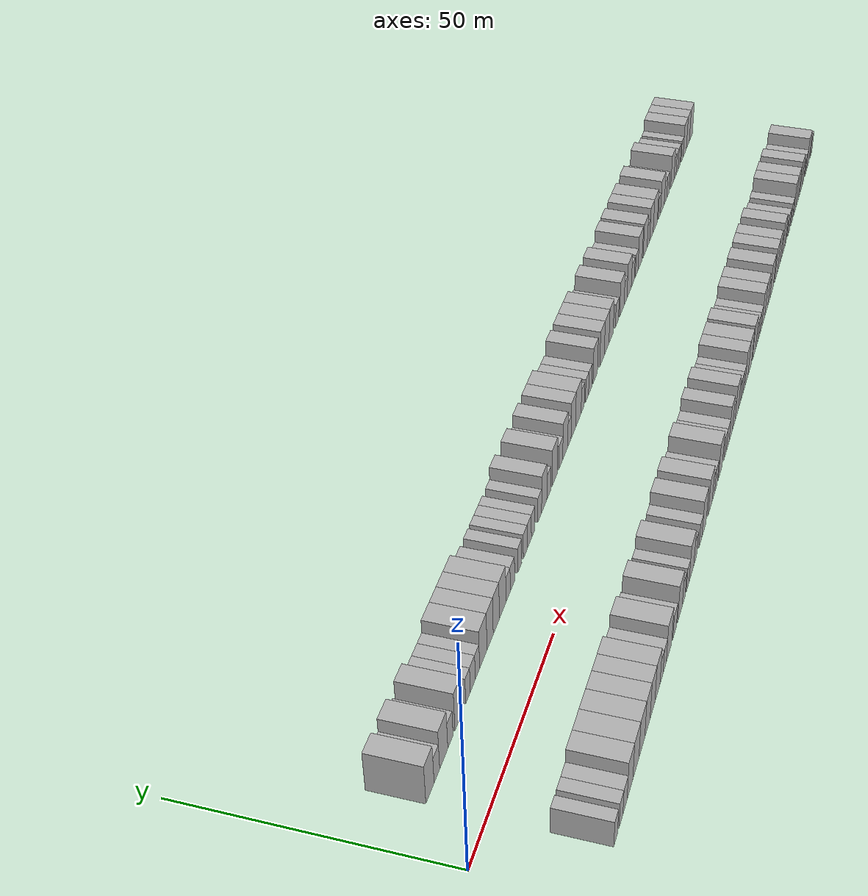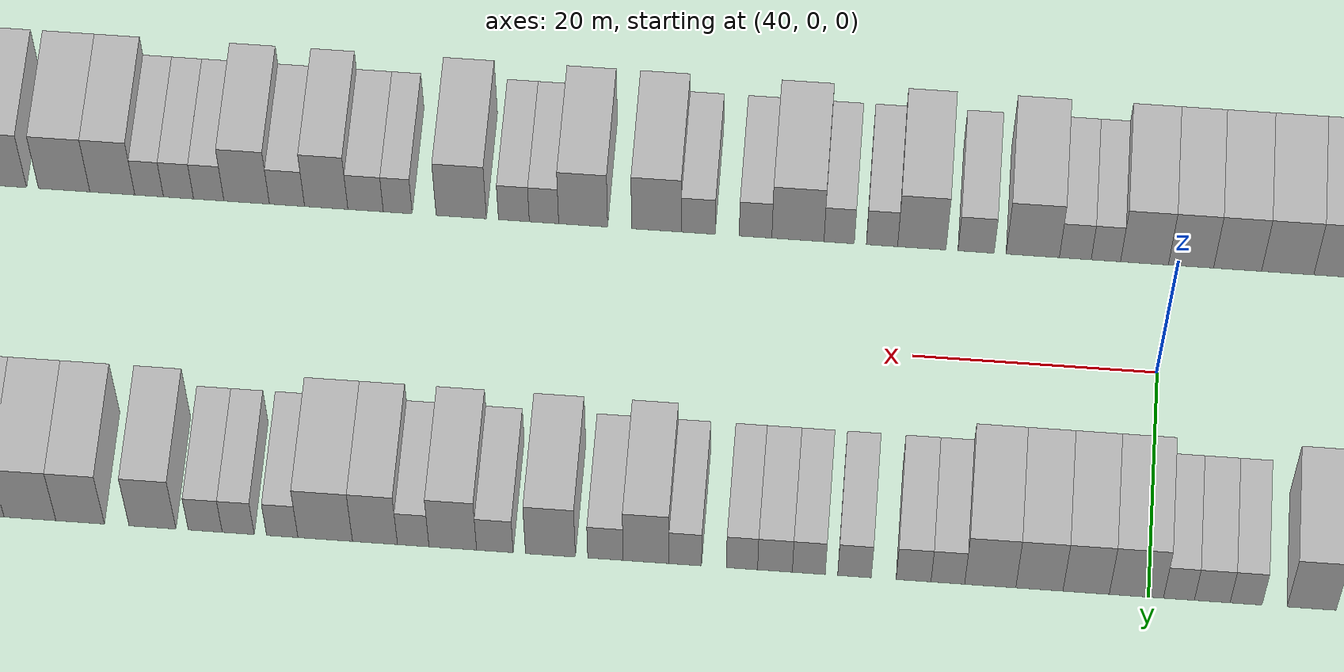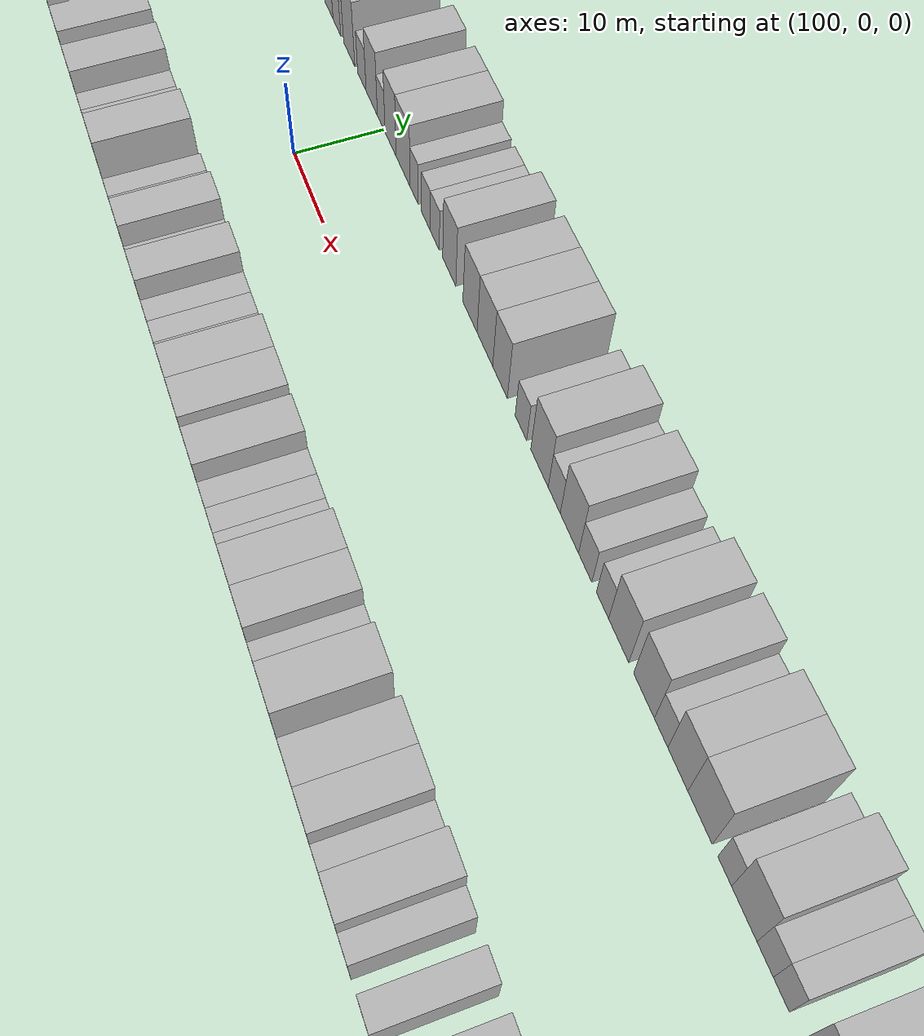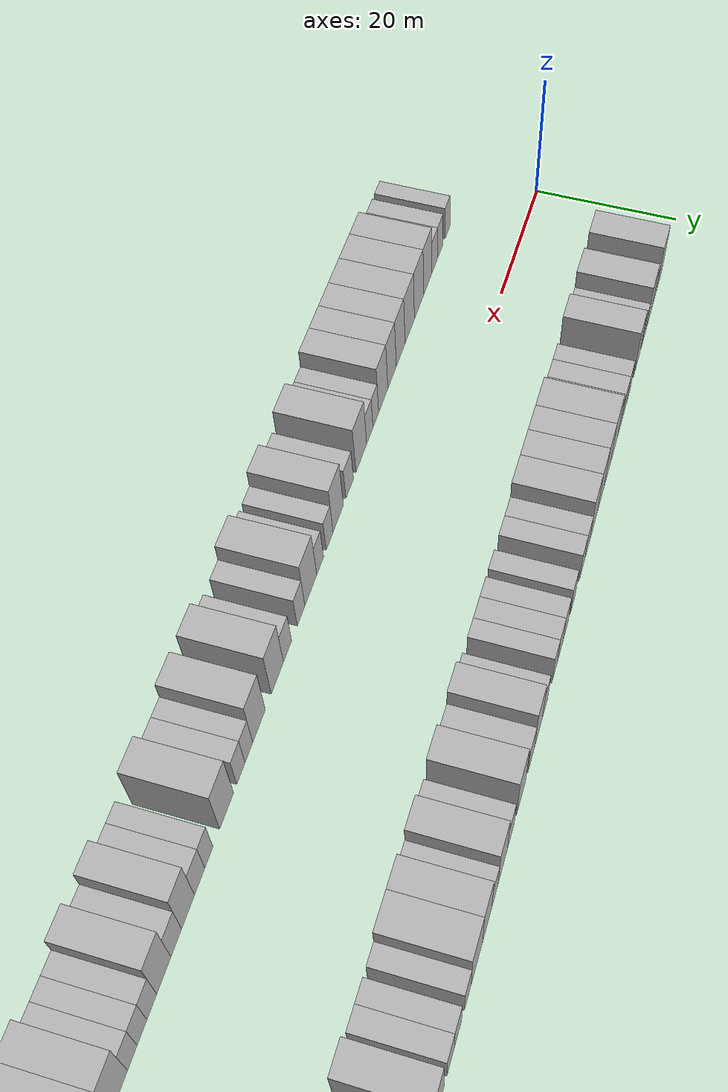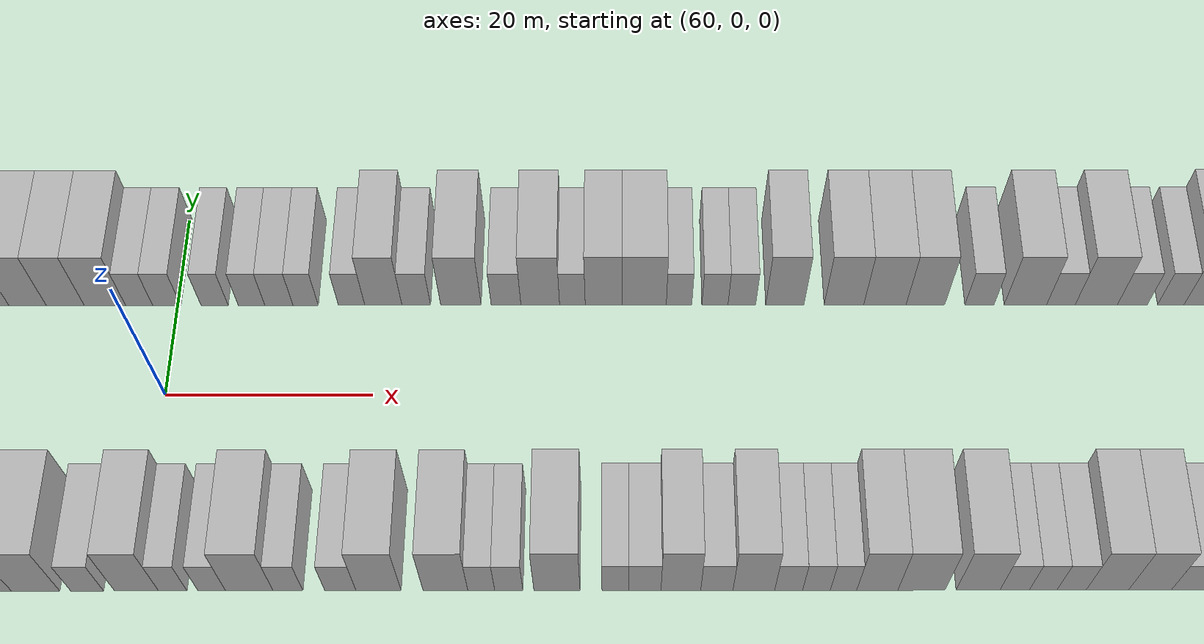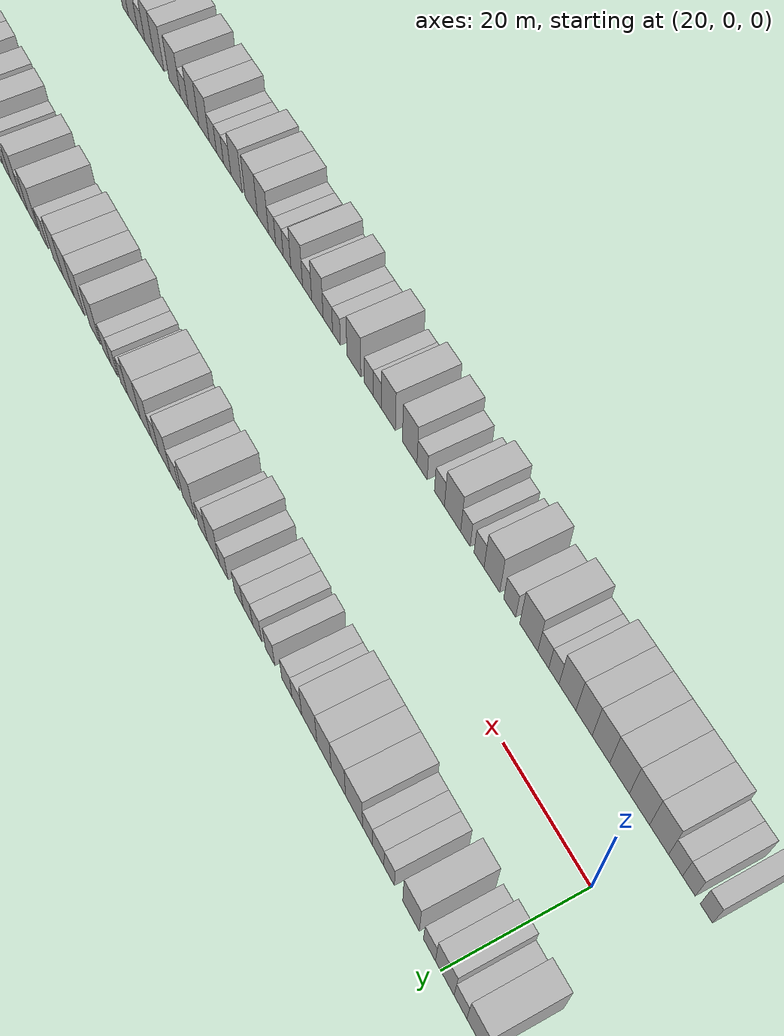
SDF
<sdf version="1.6">
 <world name="default">
  <scene>
   <sky><clouds><speed>12</speed></clouds></sky>
   <ambient>0.4 0.4 0.4 1</ambient>
   <background>0.7 0.7 0.7 1</background>
   <shadows>1</shadows>
  </scene>
  <gravity>0 0 -9.8066</gravity>
  <magnetic_field>6e-06 2.3e-05 -4.2e-05</magnetic_field>
  <physics default="0" name="default_physics" type="ode">
   <ode>
    <solver>
     <type>quick</type>
     <iters>10</iters>
     <sor>1.0</sor>
     <use_dynamic_moi_rescaling>0</use_dynamic_moi_rescaling>
    </solver>
    <constraints>
     <cfm>0</cfm>
     <erp>0.2</erp>
     <contact_max_correcting_vel>100</contact_max_correcting_vel>
     <contact_surface_layer>0.001</contact_surface_layer>
    </constraints>
   </ode>
   <max_step_size>0.004</max_step_size>
   <real_time_factor>1</real_time_factor>
   <real_time_update_rate>250</real_time_update_rate>
  </physics>
  <light name="sun" type="directional">
   <pose>0 0 10 0 0 0</pose>
   <diffuse>0.8 0.8 0.8 1</diffuse>
   <specular>0.2 0.2 0.2 1</specular>
   <attenuation>
    <range>1000</range>
    <constant>0.9</constant>
    <linear>0.01</linear>
    <quadratic>0.001</quadratic>
   </attenuation>
   <direction>-0.5 0.1 -0.9</direction>
  </light>
  <model name="building_1">
   <static>1</static>
   <pose>12.0689 15.0000 0 0.000000 0.000000 1.570796</pose>
   <link name="link">
    <pose>0 0 4.50 0 0 0</pose>
    <collision name="collision"><geometry><box><size>10.0000 4.1378 9.0000</size></box></geometry></collision>
    <visual name="visual">
     <cast_shadows>0</cast_shadows>
     <geometry><box><size>10.0000 4.1378 9.0000</size></box></geometry>
     <material>
      <script>
       <uri>model://HANNAS_wall/materials/scripts</uri>
       <uri>model://HANNAS_wall/materials/textures</uri>
       <name>vrc/HANNAS_wall</name>
      </script>
     </material>
    </visual>
   </link>
  </model>
  <model name="building_2">
   <static>1</static>
   <pose>15.5600 15.0000 0 0.000000 0.000000 1.570796</pose>
   <link name="link">
    <pose>0 0 3.00 0 0 0</pose>
    <collision name="collision"><geometry><box><size>10.0000 2.8444 6.0000</size></box></geometry></collision>
    <visual name="visual">
     <cast_shadows>0</cast_shadows>
     <geometry><box><size>10.0000 2.8444 6.0000</size></box></geometry>
     <material>
      <script>
       <uri>model://HANNAS_wall/materials/scripts</uri>
       <uri>model://HANNAS_wall/materials/textures</uri>
       <name>vrc/HANNAS_wall</name>
      </script>
     </material>
    </visual>
   </link>
  </model>
  <model name="building_3">
   <static>1</static>
   <pose>19.1028 15.0000 0 0.000000 0.000000 1.570796</pose>
   <link name="link">
    <pose>0 0 4.50 0 0 0</pose>
    <collision name="collision"><geometry><box><size>10.0000 4.2411 9.0000</size></box></geometry></collision>
    <visual name="visual">
     <cast_shadows>0</cast_shadows>
     <geometry><box><size>10.0000 4.2411 9.0000</size></box></geometry>
     <material>
      <script>
       <uri>model://HANNAS_wall/materials/scripts</uri>
       <uri>model://HANNAS_wall/materials/textures</uri>
       <name>vrc/HANNAS_wall</name>
      </script>
     </material>
    </visual>
   </link>
  </model>
  <model name="building_4">
   <static>1</static>
   <pose>22.6102 15.0000 0 0.000000 0.000000 1.570796</pose>
   <link name="link">
    <pose>0 0 3.00 0 0 0</pose>
    <collision name="collision"><geometry><box><size>10.0000 2.7738 6.0000</size></box></geometry></collision>
    <visual name="visual">
     <cast_shadows>0</cast_shadows>
     <geometry><box><size>10.0000 2.7738 6.0000</size></box></geometry>
     <material>
      <script>
       <uri>model://HANNAS_wall/materials/scripts</uri>
       <uri>model://HANNAS_wall/materials/textures</uri>
       <name>vrc/HANNAS_wall</name>
      </script>
     </material>
    </visual>
   </link>
  </model>
  <model name="building_5">
   <static>1</static>
   <pose>26.9591 15.0000 0 0.000000 0.000000 1.570796</pose>
   <link name="link">
    <pose>0 0 4.50 0 0 0</pose>
    <collision name="collision"><geometry><box><size>10.0000 3.9240 9.0000</size></box></geometry></collision>
    <visual name="visual">
     <cast_shadows>0</cast_shadows>
     <geometry><box><size>10.0000 3.9240 9.0000</size></box></geometry>
     <material>
      <script>
       <uri>model://HANNAS_wall/materials/scripts</uri>
       <uri>model://HANNAS_wall/materials/textures</uri>
       <name>vrc/HANNAS_wall</name>
      </script>
     </material>
    </visual>
   </link>
  </model>
  <model name="building_6">
   <static>1</static>
   <pose>32.1991 15.0000 0 0.000000 0.000000 1.570796</pose>
   <link name="link">
    <pose>0 0 3.00 0 0 0</pose>
    <collision name="collision"><geometry><box><size>10.0000 2.5560 6.0000</size></box></geometry></collision>
    <visual name="visual">
     <cast_shadows>0</cast_shadows>
     <geometry><box><size>10.0000 2.5560 6.0000</size></box></geometry>
     <material>
      <script>
       <uri>model://HANNAS_wall/materials/scripts</uri>
       <uri>model://HANNAS_wall/materials/textures</uri>
       <name>vrc/HANNAS_wall</name>
      </script>
     </material>
    </visual>
   </link>
  </model>
  <model name="building_7">
   <static>1</static>
   <pose>34.9066 15.0000 0 0.000000 0.000000 1.570796</pose>
   <link name="link">
    <pose>0 0 3.00 0 0 0</pose>
    <collision name="collision"><geometry><box><size>10.0000 2.8590 6.0000</size></box></geometry></collision>
    <visual name="visual">
     <cast_shadows>0</cast_shadows>
     <geometry><box><size>10.0000 2.8590 6.0000</size></box></geometry>
     <material>
      <script>
       <uri>model://HANNAS_wall/materials/scripts</uri>
       <uri>model://HANNAS_wall/materials/textures</uri>
       <name>vrc/HANNAS_wall</name>
      </script>
     </material>
    </visual>
   </link>
  </model>
  <model name="building_8">
   <static>1</static>
   <pose>37.5727 15.0000 0 0.000000 0.000000 1.570796</pose>
   <link name="link">
    <pose>0 0 3.00 0 0 0</pose>
    <collision name="collision"><geometry><box><size>10.0000 2.4732 6.0000</size></box></geometry></collision>
    <visual name="visual">
     <cast_shadows>0</cast_shadows>
     <geometry><box><size>10.0000 2.4732 6.0000</size></box></geometry>
     <material>
      <script>
       <uri>model://HANNAS_wall/materials/scripts</uri>
       <uri>model://HANNAS_wall/materials/textures</uri>
       <name>vrc/HANNAS_wall</name>
      </script>
     </material>
    </visual>
   </link>
  </model>
  <model name="building_9">
   <static>1</static>
   <pose>40.9801 15.0000 0 0.000000 0.000000 1.570796</pose>
   <link name="link">
    <pose>0 0 4.50 0 0 0</pose>
    <collision name="collision"><geometry><box><size>10.0000 4.3416 9.0000</size></box></geometry></collision>
    <visual name="visual">
     <cast_shadows>0</cast_shadows>
     <geometry><box><size>10.0000 4.3416 9.0000</size></box></geometry>
     <material>
      <script>
       <uri>model://HANNAS_wall/materials/scripts</uri>
       <uri>model://HANNAS_wall/materials/textures</uri>
       <name>vrc/HANNAS_wall</name>
      </script>
     </material>
    </visual>
   </link>
  </model>
  <model name="building_10">
   <static>1</static>
   <pose>45.0064 15.0000 0 0.000000 0.000000 1.570796</pose>
   <link name="link">
    <pose>0 0 4.50 0 0 0</pose>
    <collision name="collision"><geometry><box><size>10.0000 3.7110 9.0000</size></box></geometry></collision>
    <visual name="visual">
     <cast_shadows>0</cast_shadows>
     <geometry><box><size>10.0000 3.7110 9.0000</size></box></geometry>
     <material>
      <script>
       <uri>model://HANNAS_wall/materials/scripts</uri>
       <uri>model://HANNAS_wall/materials/textures</uri>
       <name>vrc/HANNAS_wall</name>
      </script>
     </material>
    </visual>
   </link>
  </model>
  <model name="building_11">
   <static>1</static>
   <pose>48.7529 15.0000 0 0.000000 0.000000 1.570796</pose>
   <link name="link">
    <pose>0 0 4.50 0 0 0</pose>
    <collision name="collision"><geometry><box><size>10.0000 3.7821 9.0000</size></box></geometry></collision>
    <visual name="visual">
     <cast_shadows>0</cast_shadows>
     <geometry><box><size>10.0000 3.7821 9.0000</size></box></geometry>
     <material>
      <script>
       <uri>model://HANNAS_wall/materials/scripts</uri>
       <uri>model://HANNAS_wall/materials/textures</uri>
       <name>vrc/HANNAS_wall</name>
      </script>
     </material>
    </visual>
   </link>
  </model>
  <model name="building_12">
   <static>1</static>
   <pose>52.6965 15.0000 0 0.000000 0.000000 1.570796</pose>
   <link name="link">
    <pose>0 0 4.50 0 0 0</pose>
    <collision name="collision"><geometry><box><size>10.0000 4.1051 9.0000</size></box></geometry></collision>
    <visual name="visual">
     <cast_shadows>0</cast_shadows>
     <geometry><box><size>10.0000 4.1051 9.0000</size></box></geometry>
     <material>
      <script>
       <uri>model://HANNAS_wall/materials/scripts</uri>
       <uri>model://HANNAS_wall/materials/textures</uri>
       <name>vrc/HANNAS_wall</name>
      </script>
     </material>
    </visual>
   </link>
  </model>
  <model name="building_13">
   <static>1</static>
   <pose>56.1009 15.0000 0 0.000000 0.000000 1.570796</pose>
   <link name="link">
    <pose>0 0 3.00 0 0 0</pose>
    <collision name="collision"><geometry><box><size>10.0000 2.7037 6.0000</size></box></geometry></collision>
    <visual name="visual">
     <cast_shadows>0</cast_shadows>
     <geometry><box><size>10.0000 2.7037 6.0000</size></box></geometry>
     <material>
      <script>
       <uri>model://HANNAS_wall/materials/scripts</uri>
       <uri>model://HANNAS_wall/materials/textures</uri>
       <name>vrc/HANNAS_wall</name>
      </script>
     </material>
    </visual>
   </link>
  </model>
  <model name="building_14">
   <static>1</static>
   <pose>58.8511 15.0000 0 0.000000 0.000000 1.570796</pose>
   <link name="link">
    <pose>0 0 3.00 0 0 0</pose>
    <collision name="collision"><geometry><box><size>10.0000 2.7967 6.0000</size></box></geometry></collision>
    <visual name="visual">
     <cast_shadows>0</cast_shadows>
     <geometry><box><size>10.0000 2.7967 6.0000</size></box></geometry>
     <material>
      <script>
       <uri>model://HANNAS_wall/materials/scripts</uri>
       <uri>model://HANNAS_wall/materials/textures</uri>
       <name>vrc/HANNAS_wall</name>
      </script>
     </material>
    </visual>
   </link>
  </model>
  <model name="building_15">
   <static>1</static>
   <pose>63.5975 15.0000 0 0.000000 0.000000 1.570796</pose>
   <link name="link">
    <pose>0 0 3.00 0 0 0</pose>
    <collision name="collision"><geometry><box><size>10.0000 2.6962 6.0000</size></box></geometry></collision>
    <visual name="visual">
     <cast_shadows>0</cast_shadows>
     <geometry><box><size>10.0000 2.6962 6.0000</size></box></geometry>
     <material>
      <script>
       <uri>model://HANNAS_wall/materials/scripts</uri>
       <uri>model://HANNAS_wall/materials/textures</uri>
       <name>vrc/HANNAS_wall</name>
      </script>
     </material>
    </visual>
   </link>
  </model>
  <model name="building_16">
   <static>1</static>
   <pose>67.2687 15.0000 0 0.000000 0.000000 1.570796</pose>
   <link name="link">
    <pose>0 0 3.00 0 0 0</pose>
    <collision name="collision"><geometry><box><size>10.0000 2.6462 6.0000</size></box></geometry></collision>
    <visual name="visual">
     <cast_shadows>0</cast_shadows>
     <geometry><box><size>10.0000 2.6462 6.0000</size></box></geometry>
     <material>
      <script>
       <uri>model://HANNAS_wall/materials/scripts</uri>
       <uri>model://HANNAS_wall/materials/textures</uri>
       <name>vrc/HANNAS_wall</name>
      </script>
     </material>
    </visual>
   </link>
  </model>
  <model name="building_17">
   <static>1</static>
   <pose>69.9906 15.0000 0 0.000000 0.000000 1.570796</pose>
   <link name="link">
    <pose>0 0 3.00 0 0 0</pose>
    <collision name="collision"><geometry><box><size>10.0000 2.7976 6.0000</size></box></geometry></collision>
    <visual name="visual">
     <cast_shadows>0</cast_shadows>
     <geometry><box><size>10.0000 2.7976 6.0000</size></box></geometry>
     <material>
      <script>
       <uri>model://HANNAS_wall/materials/scripts</uri>
       <uri>model://HANNAS_wall/materials/textures</uri>
       <name>vrc/HANNAS_wall</name>
      </script>
     </material>
    </visual>
   </link>
  </model>
  <model name="building_18">
   <static>1</static>
   <pose>72.6465 15.0000 0 0.000000 0.000000 1.570796</pose>
   <link name="link">
    <pose>0 0 3.00 0 0 0</pose>
    <collision name="collision"><geometry><box><size>10.0000 2.5141 6.0000</size></box></geometry></collision>
    <visual name="visual">
     <cast_shadows>0</cast_shadows>
     <geometry><box><size>10.0000 2.5141 6.0000</size></box></geometry>
     <material>
      <script>
       <uri>model://HANNAS_wall/materials/scripts</uri>
       <uri>model://HANNAS_wall/materials/textures</uri>
       <name>vrc/HANNAS_wall</name>
      </script>
     </material>
    </visual>
   </link>
  </model>
  <model name="building_19">
   <static>1</static>
   <pose>77.2143 15.0000 0 0.000000 0.000000 1.570796</pose>
   <link name="link">
    <pose>0 0 3.00 0 0 0</pose>
    <collision name="collision"><geometry><box><size>10.0000 2.6215 6.0000</size></box></geometry></collision>
    <visual name="visual">
     <cast_shadows>0</cast_shadows>
     <geometry><box><size>10.0000 2.6215 6.0000</size></box></geometry>
     <material>
      <script>
       <uri>model://HANNAS_wall/materials/scripts</uri>
       <uri>model://HANNAS_wall/materials/textures</uri>
       <name>vrc/HANNAS_wall</name>
      </script>
     </material>
    </visual>
   </link>
  </model>
  <model name="building_20">
   <static>1</static>
   <pose>80.3716 15.0000 0 0.000000 0.000000 1.570796</pose>
   <link name="link">
    <pose>0 0 4.50 0 0 0</pose>
    <collision name="collision"><geometry><box><size>10.0000 3.6931 9.0000</size></box></geometry></collision>
    <visual name="visual">
     <cast_shadows>0</cast_shadows>
     <geometry><box><size>10.0000 3.6931 9.0000</size></box></geometry>
     <material>
      <script>
       <uri>model://HANNAS_wall/materials/scripts</uri>
       <uri>model://HANNAS_wall/materials/textures</uri>
       <name>vrc/HANNAS_wall</name>
      </script>
     </material>
    </visual>
   </link>
  </model>
  <model name="building_21">
   <static>1</static>
   <pose>83.6435 15.0000 0 0.000000 0.000000 1.570796</pose>
   <link name="link">
    <pose>0 0 3.00 0 0 0</pose>
    <collision name="collision"><geometry><box><size>10.0000 2.8508 6.0000</size></box></geometry></collision>
    <visual name="visual">
     <cast_shadows>0</cast_shadows>
     <geometry><box><size>10.0000 2.8508 6.0000</size></box></geometry>
     <material>
      <script>
       <uri>model://HANNAS_wall/materials/scripts</uri>
       <uri>model://HANNAS_wall/materials/textures</uri>
       <name>vrc/HANNAS_wall</name>
      </script>
     </material>
    </visual>
   </link>
  </model>
  <model name="building_22">
   <static>1</static>
   <pose>88.0802 15.0000 0 0.000000 0.000000 1.570796</pose>
   <link name="link">
    <pose>0 0 4.50 0 0 0</pose>
    <collision name="collision"><geometry><box><size>10.0000 4.0225 9.0000</size></box></geometry></collision>
    <visual name="visual">
     <cast_shadows>0</cast_shadows>
     <geometry><box><size>10.0000 4.0225 9.0000</size></box></geometry>
     <material>
      <script>
       <uri>model://HANNAS_wall/materials/scripts</uri>
       <uri>model://HANNAS_wall/materials/textures</uri>
       <name>vrc/HANNAS_wall</name>
      </script>
     </material>
    </visual>
   </link>
  </model>
  <model name="building_23">
   <static>1</static>
   <pose>92.5674 15.0000 0 0.000000 0.000000 1.570796</pose>
   <link name="link">
    <pose>0 0 3.00 0 0 0</pose>
    <collision name="collision"><geometry><box><size>10.0000 2.9518 6.0000</size></box></geometry></collision>
    <visual name="visual">
     <cast_shadows>0</cast_shadows>
     <geometry><box><size>10.0000 2.9518 6.0000</size></box></geometry>
     <material>
      <script>
       <uri>model://HANNAS_wall/materials/scripts</uri>
       <uri>model://HANNAS_wall/materials/textures</uri>
       <name>vrc/HANNAS_wall</name>
      </script>
     </material>
    </visual>
   </link>
  </model>
  <model name="building_24">
   <static>1</static>
   <pose>95.9662 15.0000 0 0.000000 0.000000 1.570796</pose>
   <link name="link">
    <pose>0 0 4.50 0 0 0</pose>
    <collision name="collision"><geometry><box><size>10.0000 3.8458 9.0000</size></box></geometry></collision>
    <visual name="visual">
     <cast_shadows>0</cast_shadows>
     <geometry><box><size>10.0000 3.8458 9.0000</size></box></geometry>
     <material>
      <script>
       <uri>model://HANNAS_wall/materials/scripts</uri>
       <uri>model://HANNAS_wall/materials/textures</uri>
       <name>vrc/HANNAS_wall</name>
      </script>
     </material>
    </visual>
   </link>
  </model>
  <model name="building_25">
   <static>1</static>
   <pose>99.1635 15.0000 0 0.000000 0.000000 1.570796</pose>
   <link name="link">
    <pose>0 0 3.00 0 0 0</pose>
    <collision name="collision"><geometry><box><size>10.0000 2.5488 6.0000</size></box></geometry></collision>
    <visual name="visual">
     <cast_shadows>0</cast_shadows>
     <geometry><box><size>10.0000 2.5488 6.0000</size></box></geometry>
     <material>
      <script>
       <uri>model://HANNAS_wall/materials/scripts</uri>
       <uri>model://HANNAS_wall/materials/textures</uri>
       <name>vrc/HANNAS_wall</name>
      </script>
     </material>
    </visual>
   </link>
  </model>
  <model name="building_26">
   <static>1</static>
   <pose>102.2581 15.0000 0 0.000000 0.000000 1.570796</pose>
   <link name="link">
    <pose>0 0 4.50 0 0 0</pose>
    <collision name="collision"><geometry><box><size>10.0000 3.6404 9.0000</size></box></geometry></collision>
    <visual name="visual">
     <cast_shadows>0</cast_shadows>
     <geometry><box><size>10.0000 3.6404 9.0000</size></box></geometry>
     <material>
      <script>
       <uri>model://HANNAS_wall/materials/scripts</uri>
       <uri>model://HANNAS_wall/materials/textures</uri>
       <name>vrc/HANNAS_wall</name>
      </script>
     </material>
    </visual>
   </link>
  </model>
  <model name="building_27">
   <static>1</static>
   <pose>106.2851 15.0000 0 0.000000 0.000000 1.570796</pose>
   <link name="link">
    <pose>0 0 4.50 0 0 0</pose>
    <collision name="collision"><geometry><box><size>10.0000 4.4137 9.0000</size></box></geometry></collision>
    <visual name="visual">
     <cast_shadows>0</cast_shadows>
     <geometry><box><size>10.0000 4.4137 9.0000</size></box></geometry>
     <material>
      <script>
       <uri>model://HANNAS_wall/materials/scripts</uri>
       <uri>model://HANNAS_wall/materials/textures</uri>
       <name>vrc/HANNAS_wall</name>
      </script>
     </material>
    </visual>
   </link>
  </model>
  <model name="building_28">
   <static>1</static>
   <pose>109.7603 15.0000 0 0.000000 0.000000 1.570796</pose>
   <link name="link">
    <pose>0 0 3.00 0 0 0</pose>
    <collision name="collision"><geometry><box><size>10.0000 2.5368 6.0000</size></box></geometry></collision>
    <visual name="visual">
     <cast_shadows>0</cast_shadows>
     <geometry><box><size>10.0000 2.5368 6.0000</size></box></geometry>
     <material>
      <script>
       <uri>model://HANNAS_wall/materials/scripts</uri>
       <uri>model://HANNAS_wall/materials/textures</uri>
       <name>vrc/HANNAS_wall</name>
      </script>
     </material>
    </visual>
   </link>
  </model>
  <model name="building_29">
   <static>1</static>
   <pose>113.3267 15.0000 0 0.000000 0.000000 1.570796</pose>
   <link name="link">
    <pose>0 0 3.00 0 0 0</pose>
    <collision name="collision"><geometry><box><size>10.0000 2.5958 6.0000</size></box></geometry></collision>
    <visual name="visual">
     <cast_shadows>0</cast_shadows>
     <geometry><box><size>10.0000 2.5958 6.0000</size></box></geometry>
     <material>
      <script>
       <uri>model://HANNAS_wall/materials/scripts</uri>
       <uri>model://HANNAS_wall/materials/textures</uri>
       <name>vrc/HANNAS_wall</name>
      </script>
     </material>
    </visual>
   </link>
  </model>
  <model name="building_30">
   <static>1</static>
   <pose>116.0006 15.0000 0 0.000000 0.000000 1.570796</pose>
   <link name="link">
    <pose>0 0 3.00 0 0 0</pose>
    <collision name="collision"><geometry><box><size>10.0000 2.7520 6.0000</size></box></geometry></collision>
    <visual name="visual">
     <cast_shadows>0</cast_shadows>
     <geometry><box><size>10.0000 2.7520 6.0000</size></box></geometry>
     <material>
      <script>
       <uri>model://HANNAS_wall/materials/scripts</uri>
       <uri>model://HANNAS_wall/materials/textures</uri>
       <name>vrc/HANNAS_wall</name>
      </script>
     </material>
    </visual>
   </link>
  </model>
  <model name="building_31">
   <static>1</static>
   <pose>120.2804 15.0000 0 0.000000 0.000000 1.570796</pose>
   <link name="link">
    <pose>0 0 4.50 0 0 0</pose>
    <collision name="collision"><geometry><box><size>10.0000 3.8077 9.0000</size></box></geometry></collision>
    <visual name="visual">
     <cast_shadows>0</cast_shadows>
     <geometry><box><size>10.0000 3.8077 9.0000</size></box></geometry>
     <material>
      <script>
       <uri>model://HANNAS_wall/materials/scripts</uri>
       <uri>model://HANNAS_wall/materials/textures</uri>
       <name>vrc/HANNAS_wall</name>
      </script>
     </material>
    </visual>
   </link>
  </model>
  <model name="building_32">
   <static>1</static>
   <pose>126.1542 15.0000 0 0.000000 0.000000 1.570796</pose>
   <link name="link">
    <pose>0 0 4.50 0 0 0</pose>
    <collision name="collision"><geometry><box><size>10.0000 3.9397 9.0000</size></box></geometry></collision>
    <visual name="visual">
     <cast_shadows>0</cast_shadows>
     <geometry><box><size>10.0000 3.9397 9.0000</size></box></geometry>
     <material>
      <script>
       <uri>model://HANNAS_wall/materials/scripts</uri>
       <uri>model://HANNAS_wall/materials/textures</uri>
       <name>vrc/HANNAS_wall</name>
      </script>
     </material>
    </visual>
   </link>
  </model>
  <model name="building_33">
   <static>1</static>
   <pose>130.2297 15.0000 0 0.000000 0.000000 1.570796</pose>
   <link name="link">
    <pose>0 0 4.50 0 0 0</pose>
    <collision name="collision"><geometry><box><size>10.0000 4.2113 9.0000</size></box></geometry></collision>
    <visual name="visual">
     <cast_shadows>0</cast_shadows>
     <geometry><box><size>10.0000 4.2113 9.0000</size></box></geometry>
     <material>
      <script>
       <uri>model://HANNAS_wall/materials/scripts</uri>
       <uri>model://HANNAS_wall/materials/textures</uri>
       <name>vrc/HANNAS_wall</name>
      </script>
     </material>
    </visual>
   </link>
  </model>
  <model name="building_34">
   <static>1</static>
   <pose>134.2596 15.0000 0 0.000000 0.000000 1.570796</pose>
   <link name="link">
    <pose>0 0 4.50 0 0 0</pose>
    <collision name="collision"><geometry><box><size>10.0000 3.8485 9.0000</size></box></geometry></collision>
    <visual name="visual">
     <cast_shadows>0</cast_shadows>
     <geometry><box><size>10.0000 3.8485 9.0000</size></box></geometry>
     <material>
      <script>
       <uri>model://HANNAS_wall/materials/scripts</uri>
       <uri>model://HANNAS_wall/materials/textures</uri>
       <name>vrc/HANNAS_wall</name>
      </script>
     </material>
    </visual>
   </link>
  </model>
  <model name="building_35">
   <static>1</static>
   <pose>139.6347 15.0000 0 0.000000 0.000000 1.570796</pose>
   <link name="link">
    <pose>0 0 3.00 0 0 0</pose>
    <collision name="collision"><geometry><box><size>10.0000 2.9016 6.0000</size></box></geometry></collision>
    <visual name="visual">
     <cast_shadows>0</cast_shadows>
     <geometry><box><size>10.0000 2.9016 6.0000</size></box></geometry>
     <material>
      <script>
       <uri>model://HANNAS_wall/materials/scripts</uri>
       <uri>model://HANNAS_wall/materials/textures</uri>
       <name>vrc/HANNAS_wall</name>
      </script>
     </material>
    </visual>
   </link>
  </model>
  <model name="building_36">
   <static>1</static>
   <pose>144.2004 15.0000 0 0.000000 0.000000 1.570796</pose>
   <link name="link">
    <pose>0 0 4.50 0 0 0</pose>
    <collision name="collision"><geometry><box><size>10.0000 4.2298 9.0000</size></box></geometry></collision>
    <visual name="visual">
     <cast_shadows>0</cast_shadows>
     <geometry><box><size>10.0000 4.2298 9.0000</size></box></geometry>
     <material>
      <script>
       <uri>model://HANNAS_wall/materials/scripts</uri>
       <uri>model://HANNAS_wall/materials/textures</uri>
       <name>vrc/HANNAS_wall</name>
      </script>
     </material>
    </visual>
   </link>
  </model>
  <model name="building_37">
   <static>1</static>
   <pose>147.7412 15.0000 0 0.000000 0.000000 1.570796</pose>
   <link name="link">
    <pose>0 0 3.00 0 0 0</pose>
    <collision name="collision"><geometry><box><size>10.0000 2.8519 6.0000</size></box></geometry></collision>
    <visual name="visual">
     <cast_shadows>0</cast_shadows>
     <geometry><box><size>10.0000 2.8519 6.0000</size></box></geometry>
     <material>
      <script>
       <uri>model://HANNAS_wall/materials/scripts</uri>
       <uri>model://HANNAS_wall/materials/textures</uri>
       <name>vrc/HANNAS_wall</name>
      </script>
     </material>
    </visual>
   </link>
  </model>
  <model name="building_38">
   <static>1</static>
   <pose>151.2683 15.0000 0 0.000000 0.000000 1.570796</pose>
   <link name="link">
    <pose>0 0 4.50 0 0 0</pose>
    <collision name="collision"><geometry><box><size>10.0000 4.2023 9.0000</size></box></geometry></collision>
    <visual name="visual">
     <cast_shadows>0</cast_shadows>
     <geometry><box><size>10.0000 4.2023 9.0000</size></box></geometry>
     <material>
      <script>
       <uri>model://HANNAS_wall/materials/scripts</uri>
       <uri>model://HANNAS_wall/materials/textures</uri>
       <name>vrc/HANNAS_wall</name>
      </script>
     </material>
    </visual>
   </link>
  </model>
  <model name="building_39">
   <static>1</static>
   <pose>154.8601 15.0000 0 0.000000 0.000000 1.570796</pose>
   <link name="link">
    <pose>0 0 3.00 0 0 0</pose>
    <collision name="collision"><geometry><box><size>10.0000 2.9813 6.0000</size></box></geometry></collision>
    <visual name="visual">
     <cast_shadows>0</cast_shadows>
     <geometry><box><size>10.0000 2.9813 6.0000</size></box></geometry>
     <material>
      <script>
       <uri>model://HANNAS_wall/materials/scripts</uri>
       <uri>model://HANNAS_wall/materials/textures</uri>
       <name>vrc/HANNAS_wall</name>
      </script>
     </material>
    </visual>
   </link>
  </model>
  <model name="building_40">
   <static>1</static>
   <pose>158.6745 15.0000 0 0.000000 0.000000 1.570796</pose>
   <link name="link">
    <pose>0 0 3.00 0 0 0</pose>
    <collision name="collision"><geometry><box><size>10.0000 2.6474 6.0000</size></box></geometry></collision>
    <visual name="visual">
     <cast_shadows>0</cast_shadows>
     <geometry><box><size>10.0000 2.6474 6.0000</size></box></geometry>
     <material>
      <script>
       <uri>model://HANNAS_wall/materials/scripts</uri>
       <uri>model://HANNAS_wall/materials/textures</uri>
       <name>vrc/HANNAS_wall</name>
      </script>
     </material>
    </visual>
   </link>
  </model>
  <model name="building_41">
   <static>1</static>
   <pose>162.1215 15.0000 0 0.000000 0.000000 1.570796</pose>
   <link name="link">
    <pose>0 0 4.50 0 0 0</pose>
    <collision name="collision"><geometry><box><size>10.0000 4.2467 9.0000</size></box></geometry></collision>
    <visual name="visual">
     <cast_shadows>0</cast_shadows>
     <geometry><box><size>10.0000 4.2467 9.0000</size></box></geometry>
     <material>
      <script>
       <uri>model://HANNAS_wall/materials/scripts</uri>
       <uri>model://HANNAS_wall/materials/textures</uri>
       <name>vrc/HANNAS_wall</name>
      </script>
     </material>
    </visual>
   </link>
  </model>
  <model name="building_42">
   <static>1</static>
   <pose>167.3455 15.0000 0 0.000000 0.000000 1.570796</pose>
   <link name="link">
    <pose>0 0 4.50 0 0 0</pose>
    <collision name="collision"><geometry><box><size>10.0000 4.2012 9.0000</size></box></geometry></collision>
    <visual name="visual">
     <cast_shadows>0</cast_shadows>
     <geometry><box><size>10.0000 4.2012 9.0000</size></box></geometry>
     <material>
      <script>
       <uri>model://HANNAS_wall/materials/scripts</uri>
       <uri>model://HANNAS_wall/materials/textures</uri>
       <name>vrc/HANNAS_wall</name>
      </script>
     </material>
    </visual>
   </link>
  </model>
  <model name="building_43">
   <static>1</static>
   <pose>170.7555 15.0000 0 0.000000 0.000000 1.570796</pose>
   <link name="link">
    <pose>0 0 3.00 0 0 0</pose>
    <collision name="collision"><geometry><box><size>10.0000 2.6189 6.0000</size></box></geometry></collision>
    <visual name="visual">
     <cast_shadows>0</cast_shadows>
     <geometry><box><size>10.0000 2.6189 6.0000</size></box></geometry>
     <material>
      <script>
       <uri>model://HANNAS_wall/materials/scripts</uri>
       <uri>model://HANNAS_wall/materials/textures</uri>
       <name>vrc/HANNAS_wall</name>
      </script>
     </material>
    </visual>
   </link>
  </model>
  <model name="building_44">
   <static>1</static>
   <pose>173.9769 15.0000 0 0.000000 0.000000 1.570796</pose>
   <link name="link">
    <pose>0 0 4.50 0 0 0</pose>
    <collision name="collision"><geometry><box><size>10.0000 3.8240 9.0000</size></box></geometry></collision>
    <visual name="visual">
     <cast_shadows>0</cast_shadows>
     <geometry><box><size>10.0000 3.8240 9.0000</size></box></geometry>
     <material>
      <script>
       <uri>model://HANNAS_wall/materials/scripts</uri>
       <uri>model://HANNAS_wall/materials/textures</uri>
       <name>vrc/HANNAS_wall</name>
      </script>
     </material>
    </visual>
   </link>
  </model>
  <model name="building_45">
   <static>1</static>
   <pose>178.1349 15.0000 0 0.000000 0.000000 1.570796</pose>
   <link name="link">
    <pose>0 0 4.50 0 0 0</pose>
    <collision name="collision"><geometry><box><size>10.0000 4.4919 9.0000</size></box></geometry></collision>
    <visual name="visual">
     <cast_shadows>0</cast_shadows>
     <geometry><box><size>10.0000 4.4919 9.0000</size></box></geometry>
     <material>
      <script>
       <uri>model://HANNAS_wall/materials/scripts</uri>
       <uri>model://HANNAS_wall/materials/textures</uri>
       <name>vrc/HANNAS_wall</name>
      </script>
     </material>
    </visual>
   </link>
  </model>
  <model name="building_46">
   <static>1</static>
   <pose>182.5963 15.0000 0 0.000000 0.000000 1.570796</pose>
   <link name="link">
    <pose>0 0 3.00 0 0 0</pose>
    <collision name="collision"><geometry><box><size>10.0000 2.4309 6.0000</size></box></geometry></collision>
    <visual name="visual">
     <cast_shadows>0</cast_shadows>
     <geometry><box><size>10.0000 2.4309 6.0000</size></box></geometry>
     <material>
      <script>
       <uri>model://HANNAS_wall/materials/scripts</uri>
       <uri>model://HANNAS_wall/materials/textures</uri>
       <name>vrc/HANNAS_wall</name>
      </script>
     </material>
    </visual>
   </link>
  </model>
  <model name="building_47">
   <static>1</static>
   <pose>185.9915 15.0000 0 0.000000 0.000000 1.570796</pose>
   <link name="link">
    <pose>0 0 4.50 0 0 0</pose>
    <collision name="collision"><geometry><box><size>10.0000 4.3595 9.0000</size></box></geometry></collision>
    <visual name="visual">
     <cast_shadows>0</cast_shadows>
     <geometry><box><size>10.0000 4.3595 9.0000</size></box></geometry>
     <material>
      <script>
       <uri>model://HANNAS_wall/materials/scripts</uri>
       <uri>model://HANNAS_wall/materials/textures</uri>
       <name>vrc/HANNAS_wall</name>
      </script>
     </material>
    </visual>
   </link>
  </model>
  <model name="building_48">
   <static>1</static>
   <pose>189.5268 15.0000 0 0.000000 0.000000 1.570796</pose>
   <link name="link">
    <pose>0 0 3.00 0 0 0</pose>
    <collision name="collision"><geometry><box><size>10.0000 2.7111 6.0000</size></box></geometry></collision>
    <visual name="visual">
     <cast_shadows>0</cast_shadows>
     <geometry><box><size>10.0000 2.7111 6.0000</size></box></geometry>
     <material>
      <script>
       <uri>model://HANNAS_wall/materials/scripts</uri>
       <uri>model://HANNAS_wall/materials/textures</uri>
       <name>vrc/HANNAS_wall</name>
      </script>
     </material>
    </visual>
   </link>
  </model>
  <model name="building_49">
   <static>1</static>
   <pose>192.1768 15.0000 0 0.000000 0.000000 1.570796</pose>
   <link name="link">
    <pose>0 0 3.00 0 0 0</pose>
    <collision name="collision"><geometry><box><size>10.0000 2.5888 6.0000</size></box></geometry></collision>
    <visual name="visual">
     <cast_shadows>0</cast_shadows>
     <geometry><box><size>10.0000 2.5888 6.0000</size></box></geometry>
     <material>
      <script>
       <uri>model://HANNAS_wall/materials/scripts</uri>
       <uri>model://HANNAS_wall/materials/textures</uri>
       <name>vrc/HANNAS_wall</name>
      </script>
     </material>
    </visual>
   </link>
  </model>
  <model name="building_50">
   <static>1</static>
   <pose>197.3882 15.0000 0 0.000000 0.000000 1.570796</pose>
   <link name="link">
    <pose>0 0 4.50 0 0 0</pose>
    <collision name="collision"><geometry><box><size>10.0000 3.8341 9.0000</size></box></geometry></collision>
    <visual name="visual">
     <cast_shadows>0</cast_shadows>
     <geometry><box><size>10.0000 3.8341 9.0000</size></box></geometry>
     <material>
      <script>
       <uri>model://HANNAS_wall/materials/scripts</uri>
       <uri>model://HANNAS_wall/materials/textures</uri>
       <name>vrc/HANNAS_wall</name>
      </script>
     </material>
    </visual>
   </link>
  </model>
  <model name="building_51">
   <static>1</static>
   <pose>200.5221 15.0000 0 0.000000 0.000000 1.570796</pose>
   <link name="link">
    <pose>0 0 3.00 0 0 0</pose>
    <collision name="collision"><geometry><box><size>10.0000 2.4336 6.0000</size></box></geometry></collision>
    <visual name="visual">
     <cast_shadows>0</cast_shadows>
     <geometry><box><size>10.0000 2.4336 6.0000</size></box></geometry>
     <material>
      <script>
       <uri>model://HANNAS_wall/materials/scripts</uri>
       <uri>model://HANNAS_wall/materials/textures</uri>
       <name>vrc/HANNAS_wall</name>
      </script>
     </material>
    </visual>
   </link>
  </model>
  <model name="building_52">
   <static>1</static>
   <pose>202.9975 15.0000 0 0.000000 0.000000 1.570796</pose>
   <link name="link">
    <pose>0 0 3.00 0 0 0</pose>
    <collision name="collision"><geometry><box><size>10.0000 2.5173 6.0000</size></box></geometry></collision>
    <visual name="visual">
     <cast_shadows>0</cast_shadows>
     <geometry><box><size>10.0000 2.5173 6.0000</size></box></geometry>
     <material>
      <script>
       <uri>model://HANNAS_wall/materials/scripts</uri>
       <uri>model://HANNAS_wall/materials/textures</uri>
       <name>vrc/HANNAS_wall</name>
      </script>
     </material>
    </visual>
   </link>
  </model>
  <model name="building_53">
   <static>1</static>
   <pose>205.4827 15.0000 0 0.000000 0.000000 1.570796</pose>
   <link name="link">
    <pose>0 0 3.00 0 0 0</pose>
    <collision name="collision"><geometry><box><size>10.0000 2.4531 6.0000</size></box></geometry></collision>
    <visual name="visual">
     <cast_shadows>0</cast_shadows>
     <geometry><box><size>10.0000 2.4531 6.0000</size></box></geometry>
     <material>
      <script>
       <uri>model://HANNAS_wall/materials/scripts</uri>
       <uri>model://HANNAS_wall/materials/textures</uri>
       <name>vrc/HANNAS_wall</name>
      </script>
     </material>
    </visual>
   </link>
  </model>
  <model name="building_54">
   <static>1</static>
   <pose>208.9664 15.0000 0 0.000000 0.000000 1.570796</pose>
   <link name="link">
    <pose>0 0 3.00 0 0 0</pose>
    <collision name="collision"><geometry><box><size>10.0000 2.5142 6.0000</size></box></geometry></collision>
    <visual name="visual">
     <cast_shadows>0</cast_shadows>
     <geometry><box><size>10.0000 2.5142 6.0000</size></box></geometry>
     <material>
      <script>
       <uri>model://HANNAS_wall/materials/scripts</uri>
       <uri>model://HANNAS_wall/materials/textures</uri>
       <name>vrc/HANNAS_wall</name>
      </script>
     </material>
    </visual>
   </link>
  </model>
  <model name="building_55">
   <static>1</static>
   <pose>212.2727 15.0000 0 0.000000 0.000000 1.570796</pose>
   <link name="link">
    <pose>0 0 4.50 0 0 0</pose>
    <collision name="collision"><geometry><box><size>10.0000 4.0985 9.0000</size></box></geometry></collision>
    <visual name="visual">
     <cast_shadows>0</cast_shadows>
     <geometry><box><size>10.0000 4.0985 9.0000</size></box></geometry>
     <material>
      <script>
       <uri>model://HANNAS_wall/materials/scripts</uri>
       <uri>model://HANNAS_wall/materials/textures</uri>
       <name>vrc/HANNAS_wall</name>
      </script>
     </material>
    </visual>
   </link>
  </model>
  <model name="building_56">
   <static>1</static>
   <pose>216.1726 15.0000 0 0.000000 0.000000 1.570796</pose>
   <link name="link">
    <pose>0 0 4.50 0 0 0</pose>
    <collision name="collision"><geometry><box><size>10.0000 3.7013 9.0000</size></box></geometry></collision>
    <visual name="visual">
     <cast_shadows>0</cast_shadows>
     <geometry><box><size>10.0000 3.7013 9.0000</size></box></geometry>
     <material>
      <script>
       <uri>model://HANNAS_wall/materials/scripts</uri>
       <uri>model://HANNAS_wall/materials/textures</uri>
       <name>vrc/HANNAS_wall</name>
      </script>
     </material>
    </visual>
   </link>
  </model>
  <model name="building_57">
   <static>1</static>
   <pose>219.9809 15.0000 0 0.000000 0.000000 1.570796</pose>
   <link name="link">
    <pose>0 0 4.50 0 0 0</pose>
    <collision name="collision"><geometry><box><size>10.0000 3.9152 9.0000</size></box></geometry></collision>
    <visual name="visual">
     <cast_shadows>0</cast_shadows>
     <geometry><box><size>10.0000 3.9152 9.0000</size></box></geometry>
     <material>
      <script>
       <uri>model://HANNAS_wall/materials/scripts</uri>
       <uri>model://HANNAS_wall/materials/textures</uri>
       <name>vrc/HANNAS_wall</name>
      </script>
     </material>
    </visual>
   </link>
  </model>
  <model name="building_58">
   <static>1</static>
   <pose>11.2456 -15.0000 0 0.000000 0.000000 1.570796</pose>
   <link name="link">
    <pose>0 0 3.00 0 0 0</pose>
    <collision name="collision"><geometry><box><size>10.0000 2.4913 6.0000</size></box></geometry></collision>
    <visual name="visual">
     <cast_shadows>0</cast_shadows>
     <geometry><box><size>10.0000 2.4913 6.0000</size></box></geometry>
     <material>
      <script>
       <uri>model://HANNAS_wall/materials/scripts</uri>
       <uri>model://HANNAS_wall/materials/textures</uri>
       <name>vrc/HANNAS_wall</name>
      </script>
     </material>
    </visual>
   </link>
  </model>
  <model name="building_59">
   <static>1</static>
   <pose>14.8030 -15.0000 0 0.000000 0.000000 1.570796</pose>
   <link name="link">
    <pose>0 0 3.00 0 0 0</pose>
    <collision name="collision"><geometry><box><size>10.0000 2.6236 6.0000</size></box></geometry></collision>
    <visual name="visual">
     <cast_shadows>0</cast_shadows>
     <geometry><box><size>10.0000 2.6236 6.0000</size></box></geometry>
     <material>
      <script>
       <uri>model://HANNAS_wall/materials/scripts</uri>
       <uri>model://HANNAS_wall/materials/textures</uri>
       <name>vrc/HANNAS_wall</name>
      </script>
     </material>
    </visual>
   </link>
  </model>
  <model name="building_60">
   <static>1</static>
   <pose>17.5564 -15.0000 0 0.000000 0.000000 1.570796</pose>
   <link name="link">
    <pose>0 0 3.00 0 0 0</pose>
    <collision name="collision"><geometry><box><size>10.0000 2.8832 6.0000</size></box></geometry></collision>
    <visual name="visual">
     <cast_shadows>0</cast_shadows>
     <geometry><box><size>10.0000 2.8832 6.0000</size></box></geometry>
     <material>
      <script>
       <uri>model://HANNAS_wall/materials/scripts</uri>
       <uri>model://HANNAS_wall/materials/textures</uri>
       <name>vrc/HANNAS_wall</name>
      </script>
     </material>
    </visual>
   </link>
  </model>
  <model name="building_61">
   <static>1</static>
   <pose>21.0072 -15.0000 0 0.000000 0.000000 1.570796</pose>
   <link name="link">
    <pose>0 0 4.50 0 0 0</pose>
    <collision name="collision"><geometry><box><size>10.0000 4.0182 9.0000</size></box></geometry></collision>
    <visual name="visual">
     <cast_shadows>0</cast_shadows>
     <geometry><box><size>10.0000 4.0182 9.0000</size></box></geometry>
     <material>
      <script>
       <uri>model://HANNAS_wall/materials/scripts</uri>
       <uri>model://HANNAS_wall/materials/textures</uri>
       <name>vrc/HANNAS_wall</name>
      </script>
     </material>
    </visual>
   </link>
  </model>
  <model name="building_62">
   <static>1</static>
   <pose>25.1974 -15.0000 0 0.000000 0.000000 1.570796</pose>
   <link name="link">
    <pose>0 0 4.50 0 0 0</pose>
    <collision name="collision"><geometry><box><size>10.0000 4.3623 9.0000</size></box></geometry></collision>
    <visual name="visual">
     <cast_shadows>0</cast_shadows>
     <geometry><box><size>10.0000 4.3623 9.0000</size></box></geometry>
     <material>
      <script>
       <uri>model://HANNAS_wall/materials/scripts</uri>
       <uri>model://HANNAS_wall/materials/textures</uri>
       <name>vrc/HANNAS_wall</name>
      </script>
     </material>
    </visual>
   </link>
  </model>
  <model name="building_63">
   <static>1</static>
   <pose>29.5374 -15.0000 0 0.000000 0.000000 1.570796</pose>
   <link name="link">
    <pose>0 0 4.50 0 0 0</pose>
    <collision name="collision"><geometry><box><size>10.0000 4.3177 9.0000</size></box></geometry></collision>
    <visual name="visual">
     <cast_shadows>0</cast_shadows>
     <geometry><box><size>10.0000 4.3177 9.0000</size></box></geometry>
     <material>
      <script>
       <uri>model://HANNAS_wall/materials/scripts</uri>
       <uri>model://HANNAS_wall/materials/textures</uri>
       <name>vrc/HANNAS_wall</name>
      </script>
     </material>
    </visual>
   </link>
  </model>
  <model name="building_64">
   <static>1</static>
   <pose>33.6752 -15.0000 0 0.000000 0.000000 1.570796</pose>
   <link name="link">
    <pose>0 0 4.50 0 0 0</pose>
    <collision name="collision"><geometry><box><size>10.0000 3.9579 9.0000</size></box></geometry></collision>
    <visual name="visual">
     <cast_shadows>0</cast_shadows>
     <geometry><box><size>10.0000 3.9579 9.0000</size></box></geometry>
     <material>
      <script>
       <uri>model://HANNAS_wall/materials/scripts</uri>
       <uri>model://HANNAS_wall/materials/textures</uri>
       <name>vrc/HANNAS_wall</name>
      </script>
     </material>
    </visual>
   </link>
  </model>
  <model name="building_65">
   <static>1</static>
   <pose>37.5245 -15.0000 0 0.000000 0.000000 1.570796</pose>
   <link name="link">
    <pose>0 0 4.50 0 0 0</pose>
    <collision name="collision"><geometry><box><size>10.0000 3.7407 9.0000</size></box></geometry></collision>
    <visual name="visual">
     <cast_shadows>0</cast_shadows>
     <geometry><box><size>10.0000 3.7407 9.0000</size></box></geometry>
     <material>
      <script>
       <uri>model://HANNAS_wall/materials/scripts</uri>
       <uri>model://HANNAS_wall/materials/textures</uri>
       <name>vrc/HANNAS_wall</name>
      </script>
     </material>
    </visual>
   </link>
  </model>
  <model name="building_66">
   <static>1</static>
   <pose>41.3715 -15.0000 0 0.000000 0.000000 1.570796</pose>
   <link name="link">
    <pose>0 0 4.50 0 0 0</pose>
    <collision name="collision"><geometry><box><size>10.0000 3.9533 9.0000</size></box></geometry></collision>
    <visual name="visual">
     <cast_shadows>0</cast_shadows>
     <geometry><box><size>10.0000 3.9533 9.0000</size></box></geometry>
     <material>
      <script>
       <uri>model://HANNAS_wall/materials/scripts</uri>
       <uri>model://HANNAS_wall/materials/textures</uri>
       <name>vrc/HANNAS_wall</name>
      </script>
     </material>
    </visual>
   </link>
  </model>
  <model name="building_67">
   <static>1</static>
   <pose>44.5639 -15.0000 0 0.000000 0.000000 1.570796</pose>
   <link name="link">
    <pose>0 0 3.00 0 0 0</pose>
    <collision name="collision"><geometry><box><size>10.0000 2.4314 6.0000</size></box></geometry></collision>
    <visual name="visual">
     <cast_shadows>0</cast_shadows>
     <geometry><box><size>10.0000 2.4314 6.0000</size></box></geometry>
     <material>
      <script>
       <uri>model://HANNAS_wall/materials/scripts</uri>
       <uri>model://HANNAS_wall/materials/textures</uri>
       <name>vrc/HANNAS_wall</name>
      </script>
     </material>
    </visual>
   </link>
  </model>
  <model name="building_68">
   <static>1</static>
   <pose>47.0940 -15.0000 0 0.000000 0.000000 1.570796</pose>
   <link name="link">
    <pose>0 0 3.00 0 0 0</pose>
    <collision name="collision"><geometry><box><size>10.0000 2.6288 6.0000</size></box></geometry></collision>
    <visual name="visual">
     <cast_shadows>0</cast_shadows>
     <geometry><box><size>10.0000 2.6288 6.0000</size></box></geometry>
     <material>
      <script>
       <uri>model://HANNAS_wall/materials/scripts</uri>
       <uri>model://HANNAS_wall/materials/textures</uri>
       <name>vrc/HANNAS_wall</name>
      </script>
     </material>
    </visual>
   </link>
  </model>
  <model name="building_69">
   <static>1</static>
   <pose>50.6134 -15.0000 0 0.000000 0.000000 1.570796</pose>
   <link name="link">
    <pose>0 0 4.50 0 0 0</pose>
    <collision name="collision"><geometry><box><size>10.0000 4.4100 9.0000</size></box></geometry></collision>
    <visual name="visual">
     <cast_shadows>0</cast_shadows>
     <geometry><box><size>10.0000 4.4100 9.0000</size></box></geometry>
     <material>
      <script>
       <uri>model://HANNAS_wall/materials/scripts</uri>
       <uri>model://HANNAS_wall/materials/textures</uri>
       <name>vrc/HANNAS_wall</name>
      </script>
     </material>
    </visual>
   </link>
  </model>
  <model name="building_70">
   <static>1</static>
   <pose>55.3150 -15.0000 0 0.000000 0.000000 1.570796</pose>
   <link name="link">
    <pose>0 0 3.00 0 0 0</pose>
    <collision name="collision"><geometry><box><size>10.0000 2.9932 6.0000</size></box></geometry></collision>
    <visual name="visual">
     <cast_shadows>0</cast_shadows>
     <geometry><box><size>10.0000 2.9932 6.0000</size></box></geometry>
     <material>
      <script>
       <uri>model://HANNAS_wall/materials/scripts</uri>
       <uri>model://HANNAS_wall/materials/textures</uri>
       <name>vrc/HANNAS_wall</name>
      </script>
     </material>
    </visual>
   </link>
  </model>
  <model name="building_71">
   <static>1</static>
   <pose>59.8158 -15.0000 0 0.000000 0.000000 1.570796</pose>
   <link name="link">
    <pose>0 0 4.50 0 0 0</pose>
    <collision name="collision"><geometry><box><size>10.0000 4.0084 9.0000</size></box></geometry></collision>
    <visual name="visual">
     <cast_shadows>0</cast_shadows>
     <geometry><box><size>10.0000 4.0084 9.0000</size></box></geometry>
     <material>
      <script>
       <uri>model://HANNAS_wall/materials/scripts</uri>
       <uri>model://HANNAS_wall/materials/textures</uri>
       <name>vrc/HANNAS_wall</name>
      </script>
     </material>
    </visual>
   </link>
  </model>
  <model name="building_72">
   <static>1</static>
   <pose>63.1163 -15.0000 0 0.000000 0.000000 1.570796</pose>
   <link name="link">
    <pose>0 0 3.00 0 0 0</pose>
    <collision name="collision"><geometry><box><size>10.0000 2.5925 6.0000</size></box></geometry></collision>
    <visual name="visual">
     <cast_shadows>0</cast_shadows>
     <geometry><box><size>10.0000 2.5925 6.0000</size></box></geometry>
     <material>
      <script>
       <uri>model://HANNAS_wall/materials/scripts</uri>
       <uri>model://HANNAS_wall/materials/textures</uri>
       <name>vrc/HANNAS_wall</name>
      </script>
     </material>
    </visual>
   </link>
  </model>
  <model name="building_73">
   <static>1</static>
   <pose>66.6701 -15.0000 0 0.000000 0.000000 1.570796</pose>
   <link name="link">
    <pose>0 0 3.00 0 0 0</pose>
    <collision name="collision"><geometry><box><size>10.0000 2.5153 6.0000</size></box></geometry></collision>
    <visual name="visual">
     <cast_shadows>0</cast_shadows>
     <geometry><box><size>10.0000 2.5153 6.0000</size></box></geometry>
     <material>
      <script>
       <uri>model://HANNAS_wall/materials/scripts</uri>
       <uri>model://HANNAS_wall/materials/textures</uri>
       <name>vrc/HANNAS_wall</name>
      </script>
     </material>
    </visual>
   </link>
  </model>
  <model name="building_74">
   <static>1</static>
   <pose>70.0931 -15.0000 0 0.000000 0.000000 1.570796</pose>
   <link name="link">
    <pose>0 0 4.50 0 0 0</pose>
    <collision name="collision"><geometry><box><size>10.0000 4.3306 9.0000</size></box></geometry></collision>
    <visual name="visual">
     <cast_shadows>0</cast_shadows>
     <geometry><box><size>10.0000 4.3306 9.0000</size></box></geometry>
     <material>
      <script>
       <uri>model://HANNAS_wall/materials/scripts</uri>
       <uri>model://HANNAS_wall/materials/textures</uri>
       <name>vrc/HANNAS_wall</name>
      </script>
     </material>
    </visual>
   </link>
  </model>
  <model name="building_75">
   <static>1</static>
   <pose>73.6156 -15.0000 0 0.000000 0.000000 1.570796</pose>
   <link name="link">
    <pose>0 0 3.00 0 0 0</pose>
    <collision name="collision"><geometry><box><size>10.0000 2.7145 6.0000</size></box></geometry></collision>
    <visual name="visual">
     <cast_shadows>0</cast_shadows>
     <geometry><box><size>10.0000 2.7145 6.0000</size></box></geometry>
     <material>
      <script>
       <uri>model://HANNAS_wall/materials/scripts</uri>
       <uri>model://HANNAS_wall/materials/textures</uri>
       <name>vrc/HANNAS_wall</name>
      </script>
     </material>
    </visual>
   </link>
  </model>
  <model name="building_76">
   <static>1</static>
   <pose>78.3901 -15.0000 0 0.000000 0.000000 1.570796</pose>
   <link name="link">
    <pose>0 0 3.00 0 0 0</pose>
    <collision name="collision"><geometry><box><size>10.0000 2.8345 6.0000</size></box></geometry></collision>
    <visual name="visual">
     <cast_shadows>0</cast_shadows>
     <geometry><box><size>10.0000 2.8345 6.0000</size></box></geometry>
     <material>
      <script>
       <uri>model://HANNAS_wall/materials/scripts</uri>
       <uri>model://HANNAS_wall/materials/textures</uri>
       <name>vrc/HANNAS_wall</name>
      </script>
     </material>
    </visual>
   </link>
  </model>
  <model name="building_77">
   <static>1</static>
   <pose>81.8644 -15.0000 0 0.000000 0.000000 1.570796</pose>
   <link name="link">
    <pose>0 0 4.50 0 0 0</pose>
    <collision name="collision"><geometry><box><size>10.0000 4.1142 9.0000</size></box></geometry></collision>
    <visual name="visual">
     <cast_shadows>0</cast_shadows>
     <geometry><box><size>10.0000 4.1142 9.0000</size></box></geometry>
     <material>
      <script>
       <uri>model://HANNAS_wall/materials/scripts</uri>
       <uri>model://HANNAS_wall/materials/textures</uri>
       <name>vrc/HANNAS_wall</name>
      </script>
     </material>
    </visual>
   </link>
  </model>
  <model name="building_78">
   <static>1</static>
   <pose>87.9606 -15.0000 0 0.000000 0.000000 1.570796</pose>
   <link name="link">
    <pose>0 0 4.50 0 0 0</pose>
    <collision name="collision"><geometry><box><size>10.0000 4.0783 9.0000</size></box></geometry></collision>
    <visual name="visual">
     <cast_shadows>0</cast_shadows>
     <geometry><box><size>10.0000 4.0783 9.0000</size></box></geometry>
     <material>
      <script>
       <uri>model://HANNAS_wall/materials/scripts</uri>
       <uri>model://HANNAS_wall/materials/textures</uri>
       <name>vrc/HANNAS_wall</name>
      </script>
     </material>
    </visual>
   </link>
  </model>
  <model name="building_79">
   <static>1</static>
   <pose>91.2246 -15.0000 0 0.000000 0.000000 1.570796</pose>
   <link name="link">
    <pose>0 0 3.00 0 0 0</pose>
    <collision name="collision"><geometry><box><size>10.0000 2.4495 6.0000</size></box></geometry></collision>
    <visual name="visual">
     <cast_shadows>0</cast_shadows>
     <geometry><box><size>10.0000 2.4495 6.0000</size></box></geometry>
     <material>
      <script>
       <uri>model://HANNAS_wall/materials/scripts</uri>
       <uri>model://HANNAS_wall/materials/textures</uri>
       <name>vrc/HANNAS_wall</name>
      </script>
     </material>
    </visual>
   </link>
  </model>
  <model name="building_80">
   <static>1</static>
   <pose>93.7338 -15.0000 0 0.000000 0.000000 1.570796</pose>
   <link name="link">
    <pose>0 0 3.00 0 0 0</pose>
    <collision name="collision"><geometry><box><size>10.0000 2.5689 6.0000</size></box></geometry></collision>
    <visual name="visual">
     <cast_shadows>0</cast_shadows>
     <geometry><box><size>10.0000 2.5689 6.0000</size></box></geometry>
     <material>
      <script>
       <uri>model://HANNAS_wall/materials/scripts</uri>
       <uri>model://HANNAS_wall/materials/textures</uri>
       <name>vrc/HANNAS_wall</name>
      </script>
     </material>
    </visual>
   </link>
  </model>
  <model name="building_81">
   <static>1</static>
   <pose>98.1179 -15.0000 0 0.000000 0.000000 1.570796</pose>
   <link name="link">
    <pose>0 0 4.50 0 0 0</pose>
    <collision name="collision"><geometry><box><size>10.0000 4.1994 9.0000</size></box></geometry></collision>
    <visual name="visual">
     <cast_shadows>0</cast_shadows>
     <geometry><box><size>10.0000 4.1994 9.0000</size></box></geometry>
     <material>
      <script>
       <uri>model://HANNAS_wall/materials/scripts</uri>
       <uri>model://HANNAS_wall/materials/textures</uri>
       <name>vrc/HANNAS_wall</name>
      </script>
     </material>
    </visual>
   </link>
  </model>
  <model name="building_82">
   <static>1</static>
   <pose>103.4249 -15.0000 0 0.000000 0.000000 1.570796</pose>
   <link name="link">
    <pose>0 0 3.00 0 0 0</pose>
    <collision name="collision"><geometry><box><size>10.0000 2.4146 6.0000</size></box></geometry></collision>
    <visual name="visual">
     <cast_shadows>0</cast_shadows>
     <geometry><box><size>10.0000 2.4146 6.0000</size></box></geometry>
     <material>
      <script>
       <uri>model://HANNAS_wall/materials/scripts</uri>
       <uri>model://HANNAS_wall/materials/textures</uri>
       <name>vrc/HANNAS_wall</name>
      </script>
     </material>
    </visual>
   </link>
  </model>
  <model name="building_83">
   <static>1</static>
   <pose>106.1105 -15.0000 0 0.000000 0.000000 1.570796</pose>
   <link name="link">
    <pose>0 0 3.00 0 0 0</pose>
    <collision name="collision"><geometry><box><size>10.0000 2.9567 6.0000</size></box></geometry></collision>
    <visual name="visual">
     <cast_shadows>0</cast_shadows>
     <geometry><box><size>10.0000 2.9567 6.0000</size></box></geometry>
     <material>
      <script>
       <uri>model://HANNAS_wall/materials/scripts</uri>
       <uri>model://HANNAS_wall/materials/textures</uri>
       <name>vrc/HANNAS_wall</name>
      </script>
     </material>
    </visual>
   </link>
  </model>
  <model name="building_84">
   <static>1</static>
   <pose>109.3991 -15.0000 0 0.000000 0.000000 1.570796</pose>
   <link name="link">
    <pose>0 0 4.50 0 0 0</pose>
    <collision name="collision"><geometry><box><size>10.0000 3.6205 9.0000</size></box></geometry></collision>
    <visual name="visual">
     <cast_shadows>0</cast_shadows>
     <geometry><box><size>10.0000 3.6205 9.0000</size></box></geometry>
     <material>
      <script>
       <uri>model://HANNAS_wall/materials/scripts</uri>
       <uri>model://HANNAS_wall/materials/textures</uri>
       <name>vrc/HANNAS_wall</name>
      </script>
     </material>
    </visual>
   </link>
  </model>
  <model name="building_85">
   <static>1</static>
   <pose>112.6812 -15.0000 0 0.000000 0.000000 1.570796</pose>
   <link name="link">
    <pose>0 0 3.00 0 0 0</pose>
    <collision name="collision"><geometry><box><size>10.0000 2.9437 6.0000</size></box></geometry></collision>
    <visual name="visual">
     <cast_shadows>0</cast_shadows>
     <geometry><box><size>10.0000 2.9437 6.0000</size></box></geometry>
     <material>
      <script>
       <uri>model://HANNAS_wall/materials/scripts</uri>
       <uri>model://HANNAS_wall/materials/textures</uri>
       <name>vrc/HANNAS_wall</name>
      </script>
     </material>
    </visual>
   </link>
  </model>
  <model name="building_86">
   <static>1</static>
   <pose>116.0540 -15.0000 0 0.000000 0.000000 1.570796</pose>
   <link name="link">
    <pose>0 0 4.50 0 0 0</pose>
    <collision name="collision"><geometry><box><size>10.0000 3.8019 9.0000</size></box></geometry></collision>
    <visual name="visual">
     <cast_shadows>0</cast_shadows>
     <geometry><box><size>10.0000 3.8019 9.0000</size></box></geometry>
     <material>
      <script>
       <uri>model://HANNAS_wall/materials/scripts</uri>
       <uri>model://HANNAS_wall/materials/textures</uri>
       <name>vrc/HANNAS_wall</name>
      </script>
     </material>
    </visual>
   </link>
  </model>
  <model name="building_87">
   <static>1</static>
   <pose>119.2277 -15.0000 0 0.000000 0.000000 1.570796</pose>
   <link name="link">
    <pose>0 0 3.00 0 0 0</pose>
    <collision name="collision"><geometry><box><size>10.0000 2.5456 6.0000</size></box></geometry></collision>
    <visual name="visual">
     <cast_shadows>0</cast_shadows>
     <geometry><box><size>10.0000 2.5456 6.0000</size></box></geometry>
     <material>
      <script>
       <uri>model://HANNAS_wall/materials/scripts</uri>
       <uri>model://HANNAS_wall/materials/textures</uri>
       <name>vrc/HANNAS_wall</name>
      </script>
     </material>
    </visual>
   </link>
  </model>
  <model name="building_88">
   <static>1</static>
   <pose>121.7602 -15.0000 0 0.000000 0.000000 1.570796</pose>
   <link name="link">
    <pose>0 0 3.00 0 0 0</pose>
    <collision name="collision"><geometry><box><size>10.0000 2.5193 6.0000</size></box></geometry></collision>
    <visual name="visual">
     <cast_shadows>0</cast_shadows>
     <geometry><box><size>10.0000 2.5193 6.0000</size></box></geometry>
     <material>
      <script>
       <uri>model://HANNAS_wall/materials/scripts</uri>
       <uri>model://HANNAS_wall/materials/textures</uri>
       <name>vrc/HANNAS_wall</name>
      </script>
     </material>
    </visual>
   </link>
  </model>
  <model name="building_89">
   <static>1</static>
   <pose>124.2230 -15.0000 0 0.000000 0.000000 1.570796</pose>
   <link name="link">
    <pose>0 0 3.00 0 0 0</pose>
    <collision name="collision"><geometry><box><size>10.0000 2.4064 6.0000</size></box></geometry></collision>
    <visual name="visual">
     <cast_shadows>0</cast_shadows>
     <geometry><box><size>10.0000 2.4064 6.0000</size></box></geometry>
     <material>
      <script>
       <uri>model://HANNAS_wall/materials/scripts</uri>
       <uri>model://HANNAS_wall/materials/textures</uri>
       <name>vrc/HANNAS_wall</name>
      </script>
     </material>
    </visual>
   </link>
  </model>
  <model name="building_90">
   <static>1</static>
   <pose>127.3067 -15.0000 0 0.000000 0.000000 1.570796</pose>
   <link name="link">
    <pose>0 0 4.50 0 0 0</pose>
    <collision name="collision"><geometry><box><size>10.0000 3.7610 9.0000</size></box></geometry></collision>
    <visual name="visual">
     <cast_shadows>0</cast_shadows>
     <geometry><box><size>10.0000 3.7610 9.0000</size></box></geometry>
     <material>
      <script>
       <uri>model://HANNAS_wall/materials/scripts</uri>
       <uri>model://HANNAS_wall/materials/textures</uri>
       <name>vrc/HANNAS_wall</name>
      </script>
     </material>
    </visual>
   </link>
  </model>
  <model name="building_91">
   <static>1</static>
   <pose>131.3422 -15.0000 0 0.000000 0.000000 1.570796</pose>
   <link name="link">
    <pose>0 0 4.50 0 0 0</pose>
    <collision name="collision"><geometry><box><size>10.0000 4.3101 9.0000</size></box></geometry></collision>
    <visual name="visual">
     <cast_shadows>0</cast_shadows>
     <geometry><box><size>10.0000 4.3101 9.0000</size></box></geometry>
     <material>
      <script>
       <uri>model://HANNAS_wall/materials/scripts</uri>
       <uri>model://HANNAS_wall/materials/textures</uri>
       <name>vrc/HANNAS_wall</name>
      </script>
     </material>
    </visual>
   </link>
  </model>
  <model name="building_92">
   <static>1</static>
   <pose>136.4918 -15.0000 0 0.000000 0.000000 1.570796</pose>
   <link name="link">
    <pose>0 0 4.50 0 0 0</pose>
    <collision name="collision"><geometry><box><size>10.0000 3.9890 9.0000</size></box></geometry></collision>
    <visual name="visual">
     <cast_shadows>0</cast_shadows>
     <geometry><box><size>10.0000 3.9890 9.0000</size></box></geometry>
     <material>
      <script>
       <uri>model://HANNAS_wall/materials/scripts</uri>
       <uri>model://HANNAS_wall/materials/textures</uri>
       <name>vrc/HANNAS_wall</name>
      </script>
     </material>
    </visual>
   </link>
  </model>
  <model name="building_93">
   <static>1</static>
   <pose>139.8261 -15.0000 0 0.000000 0.000000 1.570796</pose>
   <link name="link">
    <pose>0 0 3.00 0 0 0</pose>
    <collision name="collision"><geometry><box><size>10.0000 2.6796 6.0000</size></box></geometry></collision>
    <visual name="visual">
     <cast_shadows>0</cast_shadows>
     <geometry><box><size>10.0000 2.6796 6.0000</size></box></geometry>
     <material>
      <script>
       <uri>model://HANNAS_wall/materials/scripts</uri>
       <uri>model://HANNAS_wall/materials/textures</uri>
       <name>vrc/HANNAS_wall</name>
      </script>
     </material>
    </visual>
   </link>
  </model>
  <model name="building_94">
   <static>1</static>
   <pose>142.4274 -15.0000 0 0.000000 0.000000 1.570796</pose>
   <link name="link">
    <pose>0 0 3.00 0 0 0</pose>
    <collision name="collision"><geometry><box><size>10.0000 2.5231 6.0000</size></box></geometry></collision>
    <visual name="visual">
     <cast_shadows>0</cast_shadows>
     <geometry><box><size>10.0000 2.5231 6.0000</size></box></geometry>
     <material>
      <script>
       <uri>model://HANNAS_wall/materials/scripts</uri>
       <uri>model://HANNAS_wall/materials/textures</uri>
       <name>vrc/HANNAS_wall</name>
      </script>
     </material>
    </visual>
   </link>
  </model>
  <model name="building_95">
   <static>1</static>
   <pose>145.0181 -15.0000 0 0.000000 0.000000 1.570796</pose>
   <link name="link">
    <pose>0 0 3.00 0 0 0</pose>
    <collision name="collision"><geometry><box><size>10.0000 2.6583 6.0000</size></box></geometry></collision>
    <visual name="visual">
     <cast_shadows>0</cast_shadows>
     <geometry><box><size>10.0000 2.6583 6.0000</size></box></geometry>
     <material>
      <script>
       <uri>model://HANNAS_wall/materials/scripts</uri>
       <uri>model://HANNAS_wall/materials/textures</uri>
       <name>vrc/HANNAS_wall</name>
      </script>
     </material>
    </visual>
   </link>
  </model>
  <model name="building_96">
   <static>1</static>
   <pose>148.2840 -15.0000 0 0.000000 0.000000 1.570796</pose>
   <link name="link">
    <pose>0 0 4.50 0 0 0</pose>
    <collision name="collision"><geometry><box><size>10.0000 3.8735 9.0000</size></box></geometry></collision>
    <visual name="visual">
     <cast_shadows>0</cast_shadows>
     <geometry><box><size>10.0000 3.8735 9.0000</size></box></geometry>
     <material>
      <script>
       <uri>model://HANNAS_wall/materials/scripts</uri>
       <uri>model://HANNAS_wall/materials/textures</uri>
       <name>vrc/HANNAS_wall</name>
      </script>
     </material>
    </visual>
   </link>
  </model>
  <model name="building_97">
   <static>1</static>
   <pose>152.1675 -15.0000 0 0.000000 0.000000 1.570796</pose>
   <link name="link">
    <pose>0 0 4.50 0 0 0</pose>
    <collision name="collision"><geometry><box><size>10.0000 3.8935 9.0000</size></box></geometry></collision>
    <visual name="visual">
     <cast_shadows>0</cast_shadows>
     <geometry><box><size>10.0000 3.8935 9.0000</size></box></geometry>
     <material>
      <script>
       <uri>model://HANNAS_wall/materials/scripts</uri>
       <uri>model://HANNAS_wall/materials/textures</uri>
       <name>vrc/HANNAS_wall</name>
      </script>
     </material>
    </visual>
   </link>
  </model>
  <model name="building_98">
   <static>1</static>
   <pose>155.6058 -15.0000 0 0.000000 0.000000 1.570796</pose>
   <link name="link">
    <pose>0 0 3.00 0 0 0</pose>
    <collision name="collision"><geometry><box><size>10.0000 2.9830 6.0000</size></box></geometry></collision>
    <visual name="visual">
     <cast_shadows>0</cast_shadows>
     <geometry><box><size>10.0000 2.9830 6.0000</size></box></geometry>
     <material>
      <script>
       <uri>model://HANNAS_wall/materials/scripts</uri>
       <uri>model://HANNAS_wall/materials/textures</uri>
       <name>vrc/HANNAS_wall</name>
      </script>
     </material>
    </visual>
   </link>
  </model>
  <model name="building_99">
   <static>1</static>
   <pose>159.3233 -15.0000 0 0.000000 0.000000 1.570796</pose>
   <link name="link">
    <pose>0 0 4.50 0 0 0</pose>
    <collision name="collision"><geometry><box><size>10.0000 4.4521 9.0000</size></box></geometry></collision>
    <visual name="visual">
     <cast_shadows>0</cast_shadows>
     <geometry><box><size>10.0000 4.4521 9.0000</size></box></geometry>
     <material>
      <script>
       <uri>model://HANNAS_wall/materials/scripts</uri>
       <uri>model://HANNAS_wall/materials/textures</uri>
       <name>vrc/HANNAS_wall</name>
      </script>
     </material>
    </visual>
   </link>
  </model>
  <model name="building_100">
   <static>1</static>
   <pose>165.5413 -15.0000 0 0.000000 0.000000 1.570796</pose>
   <link name="link">
    <pose>0 0 4.50 0 0 0</pose>
    <collision name="collision"><geometry><box><size>10.0000 3.9839 9.0000</size></box></geometry></collision>
    <visual name="visual">
     <cast_shadows>0</cast_shadows>
     <geometry><box><size>10.0000 3.9839 9.0000</size></box></geometry>
     <material>
      <script>
       <uri>model://HANNAS_wall/materials/scripts</uri>
       <uri>model://HANNAS_wall/materials/textures</uri>
       <name>vrc/HANNAS_wall</name>
      </script>
     </material>
    </visual>
   </link>
  </model>
  <model name="building_101">
   <static>1</static>
   <pose>169.3581 -15.0000 0 0.000000 0.000000 1.570796</pose>
   <link name="link">
    <pose>0 0 4.50 0 0 0</pose>
    <collision name="collision"><geometry><box><size>10.0000 3.6498 9.0000</size></box></geometry></collision>
    <visual name="visual">
     <cast_shadows>0</cast_shadows>
     <geometry><box><size>10.0000 3.6498 9.0000</size></box></geometry>
     <material>
      <script>
       <uri>model://HANNAS_wall/materials/scripts</uri>
       <uri>model://HANNAS_wall/materials/textures</uri>
       <name>vrc/HANNAS_wall</name>
      </script>
     </material>
    </visual>
   </link>
  </model>
  <model name="building_102">
   <static>1</static>
   <pose>172.6309 -15.0000 0 0.000000 0.000000 1.570796</pose>
   <link name="link">
    <pose>0 0 3.00 0 0 0</pose>
    <collision name="collision"><geometry><box><size>10.0000 2.8956 6.0000</size></box></geometry></collision>
    <visual name="visual">
     <cast_shadows>0</cast_shadows>
     <geometry><box><size>10.0000 2.8956 6.0000</size></box></geometry>
     <material>
      <script>
       <uri>model://HANNAS_wall/materials/scripts</uri>
       <uri>model://HANNAS_wall/materials/textures</uri>
       <name>vrc/HANNAS_wall</name>
      </script>
     </material>
    </visual>
   </link>
  </model>
  <model name="building_103">
   <static>1</static>
   <pose>175.9842 -15.0000 0 0.000000 0.000000 1.570796</pose>
   <link name="link">
    <pose>0 0 4.50 0 0 0</pose>
    <collision name="collision"><geometry><box><size>10.0000 3.8110 9.0000</size></box></geometry></collision>
    <visual name="visual">
     <cast_shadows>0</cast_shadows>
     <geometry><box><size>10.0000 3.8110 9.0000</size></box></geometry>
     <material>
      <script>
       <uri>model://HANNAS_wall/materials/scripts</uri>
       <uri>model://HANNAS_wall/materials/textures</uri>
       <name>vrc/HANNAS_wall</name>
      </script>
     </material>
    </visual>
   </link>
  </model>
  <model name="building_104">
   <static>1</static>
   <pose>179.1002 -15.0000 0 0.000000 0.000000 1.570796</pose>
   <link name="link">
    <pose>0 0 3.00 0 0 0</pose>
    <collision name="collision"><geometry><box><size>10.0000 2.4212 6.0000</size></box></geometry></collision>
    <visual name="visual">
     <cast_shadows>0</cast_shadows>
     <geometry><box><size>10.0000 2.4212 6.0000</size></box></geometry>
     <material>
      <script>
       <uri>model://HANNAS_wall/materials/scripts</uri>
       <uri>model://HANNAS_wall/materials/textures</uri>
       <name>vrc/HANNAS_wall</name>
      </script>
     </material>
    </visual>
   </link>
  </model>
  <model name="building_105">
   <static>1</static>
   <pose>183.7215 -15.0000 0 0.000000 0.000000 1.570796</pose>
   <link name="link">
    <pose>0 0 3.00 0 0 0</pose>
    <collision name="collision"><geometry><box><size>10.0000 2.8213 6.0000</size></box></geometry></collision>
    <visual name="visual">
     <cast_shadows>0</cast_shadows>
     <geometry><box><size>10.0000 2.8213 6.0000</size></box></geometry>
     <material>
      <script>
       <uri>model://HANNAS_wall/materials/scripts</uri>
       <uri>model://HANNAS_wall/materials/textures</uri>
       <name>vrc/HANNAS_wall</name>
      </script>
     </material>
    </visual>
   </link>
  </model>
  <model name="building_106">
   <static>1</static>
   <pose>188.5565 -15.0000 0 0.000000 0.000000 1.570796</pose>
   <link name="link">
    <pose>0 0 3.00 0 0 0</pose>
    <collision name="collision"><geometry><box><size>10.0000 2.8486 6.0000</size></box></geometry></collision>
    <visual name="visual">
     <cast_shadows>0</cast_shadows>
     <geometry><box><size>10.0000 2.8486 6.0000</size></box></geometry>
     <material>
      <script>
       <uri>model://HANNAS_wall/materials/scripts</uri>
       <uri>model://HANNAS_wall/materials/textures</uri>
       <name>vrc/HANNAS_wall</name>
      </script>
     </material>
    </visual>
   </link>
  </model>
  <model name="building_107">
   <static>1</static>
   <pose>192.8354 -15.0000 0 0.000000 0.000000 1.570796</pose>
   <link name="link">
    <pose>0 0 4.50 0 0 0</pose>
    <collision name="collision"><geometry><box><size>10.0000 3.7093 9.0000</size></box></geometry></collision>
    <visual name="visual">
     <cast_shadows>0</cast_shadows>
     <geometry><box><size>10.0000 3.7093 9.0000</size></box></geometry>
     <material>
      <script>
       <uri>model://HANNAS_wall/materials/scripts</uri>
       <uri>model://HANNAS_wall/materials/textures</uri>
       <name>vrc/HANNAS_wall</name>
      </script>
     </material>
    </visual>
   </link>
  </model>
  <model name="building_108">
   <static>1</static>
   <pose>196.6288 -15.0000 0 0.000000 0.000000 1.570796</pose>
   <link name="link">
    <pose>0 0 4.50 0 0 0</pose>
    <collision name="collision"><geometry><box><size>10.0000 3.8774 9.0000</size></box></geometry></collision>
    <visual name="visual">
     <cast_shadows>0</cast_shadows>
     <geometry><box><size>10.0000 3.8774 9.0000</size></box></geometry>
     <material>
      <script>
       <uri>model://HANNAS_wall/materials/scripts</uri>
       <uri>model://HANNAS_wall/materials/textures</uri>
       <name>vrc/HANNAS_wall</name>
      </script>
     </material>
    </visual>
   </link>
  </model>
  <model name="building_109">
   <static>1</static>
   <pose>199.7787 -15.0000 0 0.000000 0.000000 1.570796</pose>
   <link name="link">
    <pose>0 0 3.00 0 0 0</pose>
    <collision name="collision"><geometry><box><size>10.0000 2.4224 6.0000</size></box></geometry></collision>
    <visual name="visual">
     <cast_shadows>0</cast_shadows>
     <geometry><box><size>10.0000 2.4224 6.0000</size></box></geometry>
     <material>
      <script>
       <uri>model://HANNAS_wall/materials/scripts</uri>
       <uri>model://HANNAS_wall/materials/textures</uri>
       <name>vrc/HANNAS_wall</name>
      </script>
     </material>
    </visual>
   </link>
  </model>
  <model name="building_110">
   <static>1</static>
   <pose>202.7994 -15.0000 0 0.000000 0.000000 1.570796</pose>
   <link name="link">
    <pose>0 0 4.50 0 0 0</pose>
    <collision name="collision"><geometry><box><size>10.0000 3.6191 9.0000</size></box></geometry></collision>
    <visual name="visual">
     <cast_shadows>0</cast_shadows>
     <geometry><box><size>10.0000 3.6191 9.0000</size></box></geometry>
     <material>
      <script>
       <uri>model://HANNAS_wall/materials/scripts</uri>
       <uri>model://HANNAS_wall/materials/textures</uri>
       <name>vrc/HANNAS_wall</name>
      </script>
     </material>
    </visual>
   </link>
  </model>
  <model name="building_111">
   <static>1</static>
   <pose>206.0761 -15.0000 0 0.000000 0.000000 1.570796</pose>
   <link name="link">
    <pose>0 0 3.00 0 0 0</pose>
    <collision name="collision"><geometry><box><size>10.0000 2.9342 6.0000</size></box></geometry></collision>
    <visual name="visual">
     <cast_shadows>0</cast_shadows>
     <geometry><box><size>10.0000 2.9342 6.0000</size></box></geometry>
     <material>
      <script>
       <uri>model://HANNAS_wall/materials/scripts</uri>
       <uri>model://HANNAS_wall/materials/textures</uri>
       <name>vrc/HANNAS_wall</name>
      </script>
     </material>
    </visual>
   </link>
  </model>
  <model name="building_112">
   <static>1</static>
   <pose>210.7773 -15.0000 0 0.000000 0.000000 1.570796</pose>
   <link name="link">
    <pose>0 0 3.00 0 0 0</pose>
    <collision name="collision"><geometry><box><size>10.0000 2.4683 6.0000</size></box></geometry></collision>
    <visual name="visual">
     <cast_shadows>0</cast_shadows>
     <geometry><box><size>10.0000 2.4683 6.0000</size></box></geometry>
     <material>
      <script>
       <uri>model://HANNAS_wall/materials/scripts</uri>
       <uri>model://HANNAS_wall/materials/textures</uri>
       <name>vrc/HANNAS_wall</name>
      </script>
     </material>
    </visual>
   </link>
  </model>
  <model name="building_113">
   <static>1</static>
   <pose>214.1083 -15.0000 0 0.000000 0.000000 1.570796</pose>
   <link name="link">
    <pose>0 0 4.50 0 0 0</pose>
    <collision name="collision"><geometry><box><size>10.0000 4.1936 9.0000</size></box></geometry></collision>
    <visual name="visual">
     <cast_shadows>0</cast_shadows>
     <geometry><box><size>10.0000 4.1936 9.0000</size></box></geometry>
     <material>
      <script>
       <uri>model://HANNAS_wall/materials/scripts</uri>
       <uri>model://HANNAS_wall/materials/textures</uri>
       <name>vrc/HANNAS_wall</name>
      </script>
     </material>
    </visual>
   </link>
  </model>
  <model name="building_114">
   <static>1</static>
   <pose>219.6103 -15.0000 0 0.000000 0.000000 1.570796</pose>
   <link name="link">
    <pose>0 0 3.00 0 0 0</pose>
    <collision name="collision"><geometry><box><size>10.0000 2.8103 6.0000</size></box></geometry></collision>
    <visual name="visual">
     <cast_shadows>0</cast_shadows>
     <geometry><box><size>10.0000 2.8103 6.0000</size></box></geometry>
     <material>
      <script>
       <uri>model://HANNAS_wall/materials/scripts</uri>
       <uri>model://HANNAS_wall/materials/textures</uri>
       <name>vrc/HANNAS_wall</name>
      </script>
     </material>
    </visual>
   </link>
  </model>
 </world>
</sdf>
